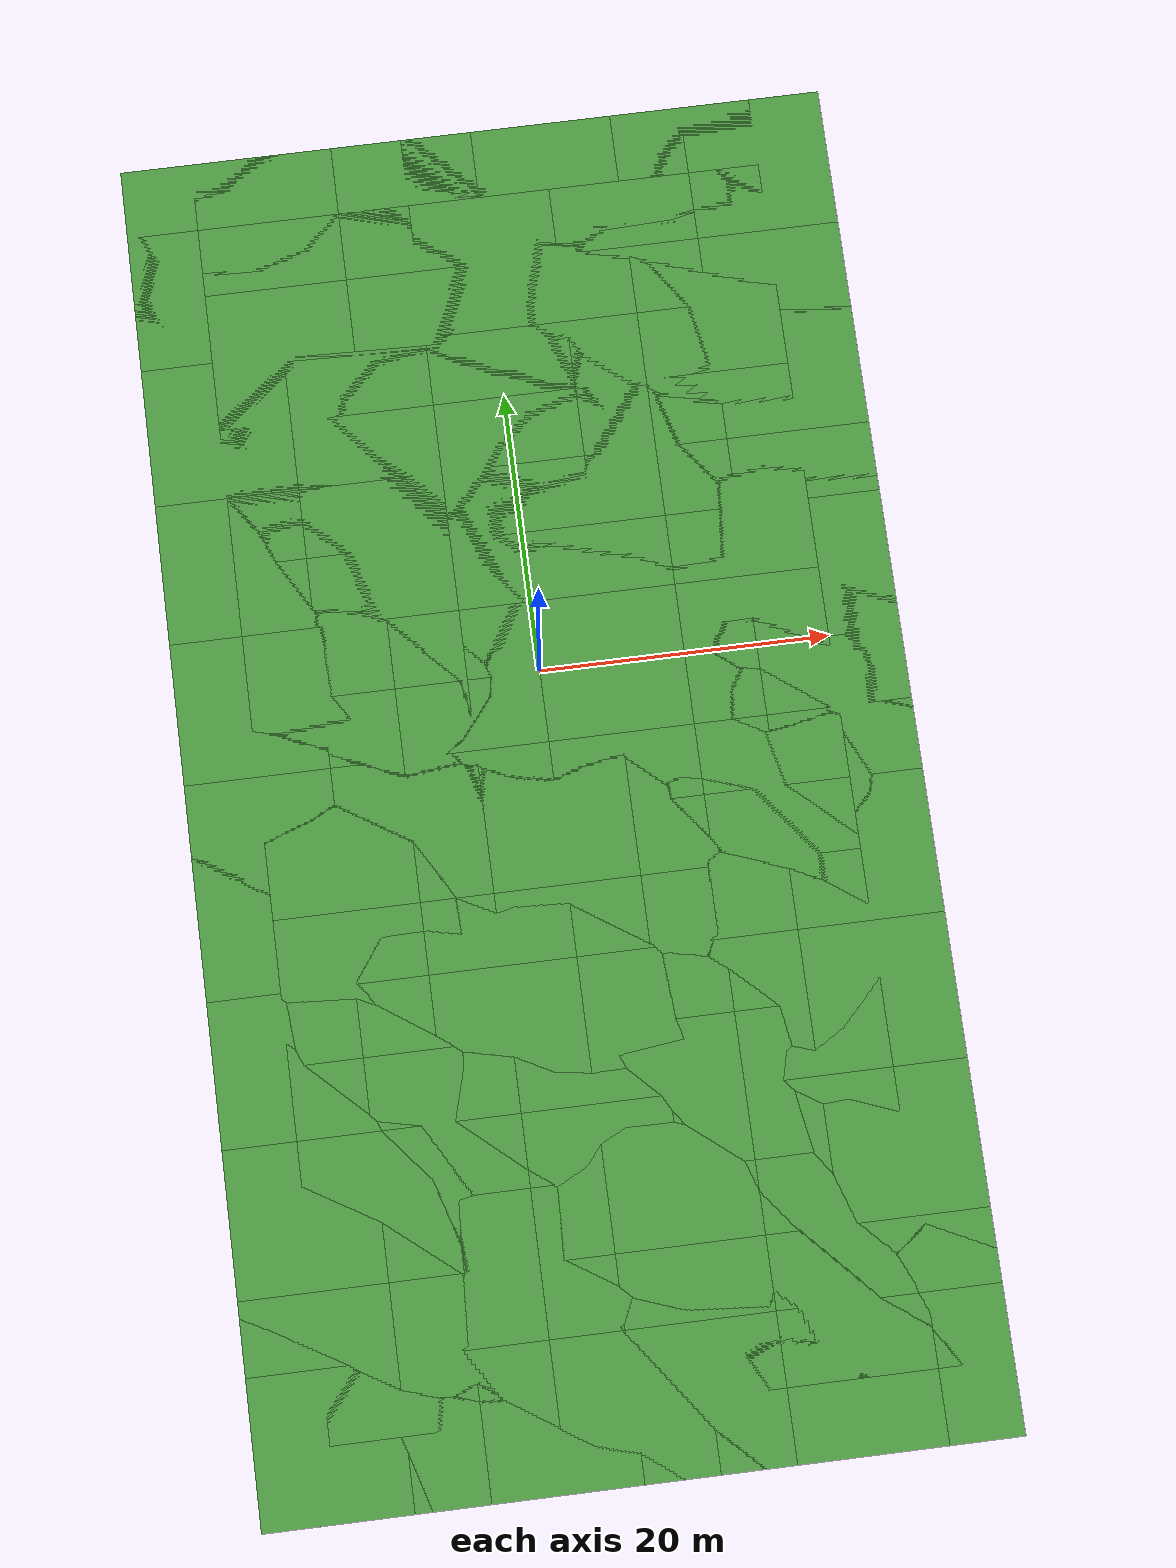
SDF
<sdf version="1.7">
 <world name="default">
  <physics name="ode_70iters" type="ode">
   <max_step_size>0.001</max_step_size>
   <real_time_update_rate>1000</real_time_update_rate>
   <ode>
    <solver>
     <type>quick</type>
     <iters>70</iters>
     <sor>1.3</sor>
     <use_dynamic_moi_rescaling>0</use_dynamic_moi_rescaling>
    </solver>
    <constraints>
     <cfm>0</cfm>
     <erp>0.2</erp>
     <contact_max_correcting_vel>100</contact_max_correcting_vel>
     <contact_surface_layer>0.001</contact_surface_layer>
    </constraints>
   </ode>
   <real_time_factor>1</real_time_factor>
  </physics>
  <model name="garden">
   <static>1</static>
   <pose>0 0 0 0 -0 1.57</pose>
   <frame name="garden_0::__model__" attached_to="garden_0::link">
    <pose relative_to="__model__">0 0 0 0 -0 0</pose>
   </frame>
   <static>1</static>
   <link name="garden_0::link">
    <collision name="collision">
     <geometry><plane><normal>0 0 1</normal><size>100 100</size></plane></geometry>
     <surface><friction><ode><mu>100</mu><mu2>50</mu2></ode></friction></surface>
    </collision>
    <visual name="visual_0">
     <cast_shadows>0</cast_shadows>
     <geometry><plane><normal>0 0 1</normal><size>10 10</size></plane></geometry>
     <material>
      <script>
       <uri>model://garden/materials/scripts</uri>
       <uri>model://garden/materials/textures</uri>
       <name>vrc/grass</name>
      </script>
     </material>
    </visual>
    <visual name="visual_1">
     <pose>5 0 0 0 -0 0</pose>
     <cast_shadows>0</cast_shadows>
     <geometry><plane><normal>0 0 1</normal><size>10 10</size></plane></geometry>
     <material>
      <script>
       <uri>model://garden/materials/scripts</uri>
       <uri>model://garden/materials/textures</uri>
       <name>vrc/grass</name>
      </script>
     </material>
    </visual>
    <visual name="visual_2">
     <pose>0 5 0 0 -0 0</pose>
     <cast_shadows>0</cast_shadows>
     <geometry><plane><normal>0 0 1</normal><size>10 10</size></plane></geometry>
     <material>
      <script>
       <uri>model://garden/materials/scripts</uri>
       <uri>model://garden/materials/textures</uri>
       <name>vrc/grass</name>
      </script>
     </material>
    </visual>
    <visual name="visual_3">
     <pose>-5 0 0 0 -0 0</pose>
     <cast_shadows>0</cast_shadows>
     <geometry><plane><normal>0 0 1</normal><size>10 10</size></plane></geometry>
     <material>
      <script>
       <uri>model://garden/materials/scripts</uri>
       <uri>model://garden/materials/textures</uri>
       <name>vrc/grass</name>
      </script>
     </material>
    </visual>
    <visual name="visual_4">
     <pose>0 -5 0 0 -0 0</pose>
     <cast_shadows>0</cast_shadows>
     <geometry><plane><normal>0 0 1</normal><size>10 10</size></plane></geometry>
     <material>
      <script>
       <uri>model://garden/materials/scripts</uri>
       <uri>model://garden/materials/textures</uri>
       <name>vrc/grass</name>
      </script>
     </material>
    </visual>
    <visual name="visual_5">
     <pose>5 5 0 0 -0 0</pose>
     <cast_shadows>0</cast_shadows>
     <geometry><plane><normal>0 0 1</normal><size>10 10</size></plane></geometry>
     <material>
      <script>
       <uri>model://garden/materials/scripts</uri>
       <uri>model://garden/materials/textures</uri>
       <name>vrc/grass</name>
      </script>
     </material>
    </visual>
    <visual name="visual_6">
     <pose>-5 -5 0 0 -0 0</pose>
     <cast_shadows>0</cast_shadows>
     <geometry><plane><normal>0 0 1</normal><size>10 10</size></plane></geometry>
     <material>
      <script>
       <uri>model://garden/materials/scripts</uri>
       <uri>model://garden/materials/textures</uri>
       <name>vrc/grass</name>
      </script>
     </material>
    </visual>
    <visual name="visual_7">
     <pose>5 -5 0 0 -0 0</pose>
     <cast_shadows>0</cast_shadows>
     <geometry><plane><normal>0 0 1</normal><size>10 10</size></plane></geometry>
     <material>
      <script>
       <uri>model://garden/materials/scripts</uri>
       <uri>model://garden/materials/textures</uri>
       <name>vrc/grass</name>
      </script>
     </material>
    </visual>
    <visual name="visual_8">
     <pose>-5 5 0 0 -0 0</pose>
     <cast_shadows>0</cast_shadows>
     <geometry><plane><normal>0 0 1</normal><size>10 10</size></plane></geometry>
     <material>
      <script>
       <uri>model://garden/materials/scripts</uri>
       <uri>model://garden/materials/textures</uri>
       <name>vrc/grass</name>
      </script>
     </material>
    </visual>
    <pose relative_to="garden_0::__model__">0 0 0 0 -0 0</pose>
   </link>
   <frame name="garden_1::__model__" attached_to="garden_1::link">
    <pose relative_to="__model__">15 0 0 0 -0 0</pose>
   </frame>
   <static>1</static>
   <link name="garden_1::link">
    <collision name="collision">
     <geometry><plane><normal>0 0 1</normal><size>100 100</size></plane></geometry>
     <surface><friction><ode><mu>100</mu><mu2>50</mu2></ode></friction></surface>
    </collision>
    <visual name="visual_0">
     <cast_shadows>0</cast_shadows>
     <geometry><plane><normal>0 0 1</normal><size>10 10</size></plane></geometry>
     <material>
      <script>
       <uri>model://garden/materials/scripts</uri>
       <uri>model://garden/materials/textures</uri>
       <name>vrc/grass</name>
      </script>
     </material>
    </visual>
    <visual name="visual_1">
     <pose>5 0 0 0 -0 0</pose>
     <cast_shadows>0</cast_shadows>
     <geometry><plane><normal>0 0 1</normal><size>10 10</size></plane></geometry>
     <material>
      <script>
       <uri>model://garden/materials/scripts</uri>
       <uri>model://garden/materials/textures</uri>
       <name>vrc/grass</name>
      </script>
     </material>
    </visual>
    <visual name="visual_2">
     <pose>0 5 0 0 -0 0</pose>
     <cast_shadows>0</cast_shadows>
     <geometry><plane><normal>0 0 1</normal><size>10 10</size></plane></geometry>
     <material>
      <script>
       <uri>model://garden/materials/scripts</uri>
       <uri>model://garden/materials/textures</uri>
       <name>vrc/grass</name>
      </script>
     </material>
    </visual>
    <visual name="visual_3">
     <pose>-5 0 0 0 -0 0</pose>
     <cast_shadows>0</cast_shadows>
     <geometry><plane><normal>0 0 1</normal><size>10 10</size></plane></geometry>
     <material>
      <script>
       <uri>model://garden/materials/scripts</uri>
       <uri>model://garden/materials/textures</uri>
       <name>vrc/grass</name>
      </script>
     </material>
    </visual>
    <visual name="visual_4">
     <pose>0 -5 0 0 -0 0</pose>
     <cast_shadows>0</cast_shadows>
     <geometry><plane><normal>0 0 1</normal><size>10 10</size></plane></geometry>
     <material>
      <script>
       <uri>model://garden/materials/scripts</uri>
       <uri>model://garden/materials/textures</uri>
       <name>vrc/grass</name>
      </script>
     </material>
    </visual>
    <visual name="visual_5">
     <pose>5 5 0 0 -0 0</pose>
     <cast_shadows>0</cast_shadows>
     <geometry><plane><normal>0 0 1</normal><size>10 10</size></plane></geometry>
     <material>
      <script>
       <uri>model://garden/materials/scripts</uri>
       <uri>model://garden/materials/textures</uri>
       <name>vrc/grass</name>
      </script>
     </material>
    </visual>
    <visual name="visual_6">
     <pose>-5 -5 0 0 -0 0</pose>
     <cast_shadows>0</cast_shadows>
     <geometry><plane><normal>0 0 1</normal><size>10 10</size></plane></geometry>
     <material>
      <script>
       <uri>model://garden/materials/scripts</uri>
       <uri>model://garden/materials/textures</uri>
       <name>vrc/grass</name>
      </script>
     </material>
    </visual>
    <visual name="visual_7">
     <pose>5 -5 0 0 -0 0</pose>
     <cast_shadows>0</cast_shadows>
     <geometry><plane><normal>0 0 1</normal><size>10 10</size></plane></geometry>
     <material>
      <script>
       <uri>model://garden/materials/scripts</uri>
       <uri>model://garden/materials/textures</uri>
       <name>vrc/grass</name>
      </script>
     </material>
    </visual>
    <visual name="visual_8">
     <pose>-5 5 0 0 -0 0</pose>
     <cast_shadows>0</cast_shadows>
     <geometry><plane><normal>0 0 1</normal><size>10 10</size></plane></geometry>
     <material>
      <script>
       <uri>model://garden/materials/scripts</uri>
       <uri>model://garden/materials/textures</uri>
       <name>vrc/grass</name>
      </script>
     </material>
    </visual>
    <pose relative_to="garden_1::__model__">0 0 0 0 -0 0</pose>
   </link>
   <frame name="garden_2::__model__" attached_to="garden_2::link">
    <pose relative_to="__model__">0 15 0 0 -0 0</pose>
   </frame>
   <static>1</static>
   <link name="garden_2::link">
    <collision name="collision">
     <geometry><plane><normal>0 0 1</normal><size>100 100</size></plane></geometry>
     <surface><friction><ode><mu>100</mu><mu2>50</mu2></ode></friction></surface>
    </collision>
    <visual name="visual_0">
     <cast_shadows>0</cast_shadows>
     <geometry><plane><normal>0 0 1</normal><size>10 10</size></plane></geometry>
     <material>
      <script>
       <uri>model://garden/materials/scripts</uri>
       <uri>model://garden/materials/textures</uri>
       <name>vrc/grass</name>
      </script>
     </material>
    </visual>
    <visual name="visual_1">
     <pose>5 0 0 0 -0 0</pose>
     <cast_shadows>0</cast_shadows>
     <geometry><plane><normal>0 0 1</normal><size>10 10</size></plane></geometry>
     <material>
      <script>
       <uri>model://garden/materials/scripts</uri>
       <uri>model://garden/materials/textures</uri>
       <name>vrc/grass</name>
      </script>
     </material>
    </visual>
    <visual name="visual_2">
     <pose>0 5 0 0 -0 0</pose>
     <cast_shadows>0</cast_shadows>
     <geometry><plane><normal>0 0 1</normal><size>10 10</size></plane></geometry>
     <material>
      <script>
       <uri>model://garden/materials/scripts</uri>
       <uri>model://garden/materials/textures</uri>
       <name>vrc/grass</name>
      </script>
     </material>
    </visual>
    <visual name="visual_3">
     <pose>-5 0 0 0 -0 0</pose>
     <cast_shadows>0</cast_shadows>
     <geometry><plane><normal>0 0 1</normal><size>10 10</size></plane></geometry>
     <material>
      <script>
       <uri>model://garden/materials/scripts</uri>
       <uri>model://garden/materials/textures</uri>
       <name>vrc/grass</name>
      </script>
     </material>
    </visual>
    <visual name="visual_4">
     <pose>0 -5 0 0 -0 0</pose>
     <cast_shadows>0</cast_shadows>
     <geometry><plane><normal>0 0 1</normal><size>10 10</size></plane></geometry>
     <material>
      <script>
       <uri>model://garden/materials/scripts</uri>
       <uri>model://garden/materials/textures</uri>
       <name>vrc/grass</name>
      </script>
     </material>
    </visual>
    <visual name="visual_5">
     <pose>5 5 0 0 -0 0</pose>
     <cast_shadows>0</cast_shadows>
     <geometry><plane><normal>0 0 1</normal><size>10 10</size></plane></geometry>
     <material>
      <script>
       <uri>model://garden/materials/scripts</uri>
       <uri>model://garden/materials/textures</uri>
       <name>vrc/grass</name>
      </script>
     </material>
    </visual>
    <visual name="visual_6">
     <pose>-5 -5 0 0 -0 0</pose>
     <cast_shadows>0</cast_shadows>
     <geometry><plane><normal>0 0 1</normal><size>10 10</size></plane></geometry>
     <material>
      <script>
       <uri>model://garden/materials/scripts</uri>
       <uri>model://garden/materials/textures</uri>
       <name>vrc/grass</name>
      </script>
     </material>
    </visual>
    <visual name="visual_7">
     <pose>5 -5 0 0 -0 0</pose>
     <cast_shadows>0</cast_shadows>
     <geometry><plane><normal>0 0 1</normal><size>10 10</size></plane></geometry>
     <material>
      <script>
       <uri>model://garden/materials/scripts</uri>
       <uri>model://garden/materials/textures</uri>
       <name>vrc/grass</name>
      </script>
     </material>
    </visual>
    <visual name="visual_8">
     <pose>-5 5 0 0 -0 0</pose>
     <cast_shadows>0</cast_shadows>
     <geometry><plane><normal>0 0 1</normal><size>10 10</size></plane></geometry>
     <material>
      <script>
       <uri>model://garden/materials/scripts</uri>
       <uri>model://garden/materials/textures</uri>
       <name>vrc/grass</name>
      </script>
     </material>
    </visual>
    <pose relative_to="garden_2::__model__">0 0 0 0 -0 0</pose>
   </link>
   <frame name="garden_3::__model__" attached_to="garden_3::link">
    <pose relative_to="__model__">0 -15 0 0 -0 0</pose>
   </frame>
   <static>1</static>
   <link name="garden_3::link">
    <collision name="collision">
     <geometry><plane><normal>0 0 1</normal><size>100 100</size></plane></geometry>
     <surface><friction><ode><mu>100</mu><mu2>50</mu2></ode></friction></surface>
    </collision>
    <visual name="visual_0">
     <cast_shadows>0</cast_shadows>
     <geometry><plane><normal>0 0 1</normal><size>10 10</size></plane></geometry>
     <material>
      <script>
       <uri>model://garden/materials/scripts</uri>
       <uri>model://garden/materials/textures</uri>
       <name>vrc/grass</name>
      </script>
     </material>
    </visual>
    <visual name="visual_1">
     <pose>5 0 0 0 -0 0</pose>
     <cast_shadows>0</cast_shadows>
     <geometry><plane><normal>0 0 1</normal><size>10 10</size></plane></geometry>
     <material>
      <script>
       <uri>model://garden/materials/scripts</uri>
       <uri>model://garden/materials/textures</uri>
       <name>vrc/grass</name>
      </script>
     </material>
    </visual>
    <visual name="visual_2">
     <pose>0 5 0 0 -0 0</pose>
     <cast_shadows>0</cast_shadows>
     <geometry><plane><normal>0 0 1</normal><size>10 10</size></plane></geometry>
     <material>
      <script>
       <uri>model://garden/materials/scripts</uri>
       <uri>model://garden/materials/textures</uri>
       <name>vrc/grass</name>
      </script>
     </material>
    </visual>
    <visual name="visual_3">
     <pose>-5 0 0 0 -0 0</pose>
     <cast_shadows>0</cast_shadows>
     <geometry><plane><normal>0 0 1</normal><size>10 10</size></plane></geometry>
     <material>
      <script>
       <uri>model://garden/materials/scripts</uri>
       <uri>model://garden/materials/textures</uri>
       <name>vrc/grass</name>
      </script>
     </material>
    </visual>
    <visual name="visual_4">
     <pose>0 -5 0 0 -0 0</pose>
     <cast_shadows>0</cast_shadows>
     <geometry><plane><normal>0 0 1</normal><size>10 10</size></plane></geometry>
     <material>
      <script>
       <uri>model://garden/materials/scripts</uri>
       <uri>model://garden/materials/textures</uri>
       <name>vrc/grass</name>
      </script>
     </material>
    </visual>
    <visual name="visual_5">
     <pose>5 5 0 0 -0 0</pose>
     <cast_shadows>0</cast_shadows>
     <geometry><plane><normal>0 0 1</normal><size>10 10</size></plane></geometry>
     <material>
      <script>
       <uri>model://garden/materials/scripts</uri>
       <uri>model://garden/materials/textures</uri>
       <name>vrc/grass</name>
      </script>
     </material>
    </visual>
    <visual name="visual_6">
     <pose>-5 -5 0 0 -0 0</pose>
     <cast_shadows>0</cast_shadows>
     <geometry><plane><normal>0 0 1</normal><size>10 10</size></plane></geometry>
     <material>
      <script>
       <uri>model://garden/materials/scripts</uri>
       <uri>model://garden/materials/textures</uri>
       <name>vrc/grass</name>
      </script>
     </material>
    </visual>
    <visual name="visual_7">
     <pose>5 -5 0 0 -0 0</pose>
     <cast_shadows>0</cast_shadows>
     <geometry><plane><normal>0 0 1</normal><size>10 10</size></plane></geometry>
     <material>
      <script>
       <uri>model://garden/materials/scripts</uri>
       <uri>model://garden/materials/textures</uri>
       <name>vrc/grass</name>
      </script>
     </material>
    </visual>
    <visual name="visual_8">
     <pose>-5 5 0 0 -0 0</pose>
     <cast_shadows>0</cast_shadows>
     <geometry><plane><normal>0 0 1</normal><size>10 10</size></plane></geometry>
     <material>
      <script>
       <uri>model://garden/materials/scripts</uri>
       <uri>model://garden/materials/textures</uri>
       <name>vrc/grass</name>
      </script>
     </material>
    </visual>
    <pose relative_to="garden_3::__model__">0 0 0 0 -0 0</pose>
   </link>
   <frame name="garden_4::__model__" attached_to="garden_4::link">
    <pose relative_to="__model__">-15 0 0 0 -0 0</pose>
   </frame>
   <static>1</static>
   <link name="garden_4::link">
    <collision name="collision">
     <geometry><plane><normal>0 0 1</normal><size>100 100</size></plane></geometry>
     <surface><friction><ode><mu>100</mu><mu2>50</mu2></ode></friction></surface>
    </collision>
    <visual name="visual_0">
     <cast_shadows>0</cast_shadows>
     <geometry><plane><normal>0 0 1</normal><size>10 10</size></plane></geometry>
     <material>
      <script>
       <uri>model://garden/materials/scripts</uri>
       <uri>model://garden/materials/textures</uri>
       <name>vrc/grass</name>
      </script>
     </material>
    </visual>
    <visual name="visual_1">
     <pose>5 0 0 0 -0 0</pose>
     <cast_shadows>0</cast_shadows>
     <geometry><plane><normal>0 0 1</normal><size>10 10</size></plane></geometry>
     <material>
      <script>
       <uri>model://garden/materials/scripts</uri>
       <uri>model://garden/materials/textures</uri>
       <name>vrc/grass</name>
      </script>
     </material>
    </visual>
    <visual name="visual_2">
     <pose>0 5 0 0 -0 0</pose>
     <cast_shadows>0</cast_shadows>
     <geometry><plane><normal>0 0 1</normal><size>10 10</size></plane></geometry>
     <material>
      <script>
       <uri>model://garden/materials/scripts</uri>
       <uri>model://garden/materials/textures</uri>
       <name>vrc/grass</name>
      </script>
     </material>
    </visual>
    <visual name="visual_3">
     <pose>-5 0 0 0 -0 0</pose>
     <cast_shadows>0</cast_shadows>
     <geometry><plane><normal>0 0 1</normal><size>10 10</size></plane></geometry>
     <material>
      <script>
       <uri>model://garden/materials/scripts</uri>
       <uri>model://garden/materials/textures</uri>
       <name>vrc/grass</name>
      </script>
     </material>
    </visual>
    <visual name="visual_4">
     <pose>0 -5 0 0 -0 0</pose>
     <cast_shadows>0</cast_shadows>
     <geometry><plane><normal>0 0 1</normal><size>10 10</size></plane></geometry>
     <material>
      <script>
       <uri>model://garden/materials/scripts</uri>
       <uri>model://garden/materials/textures</uri>
       <name>vrc/grass</name>
      </script>
     </material>
    </visual>
    <visual name="visual_5">
     <pose>5 5 0 0 -0 0</pose>
     <cast_shadows>0</cast_shadows>
     <geometry><plane><normal>0 0 1</normal><size>10 10</size></plane></geometry>
     <material>
      <script>
       <uri>model://garden/materials/scripts</uri>
       <uri>model://garden/materials/textures</uri>
       <name>vrc/grass</name>
      </script>
     </material>
    </visual>
    <visual name="visual_6">
     <pose>-5 -5 0 0 -0 0</pose>
     <cast_shadows>0</cast_shadows>
     <geometry><plane><normal>0 0 1</normal><size>10 10</size></plane></geometry>
     <material>
      <script>
       <uri>model://garden/materials/scripts</uri>
       <uri>model://garden/materials/textures</uri>
       <name>vrc/grass</name>
      </script>
     </material>
    </visual>
    <visual name="visual_7">
     <pose>5 -5 0 0 -0 0</pose>
     <cast_shadows>0</cast_shadows>
     <geometry><plane><normal>0 0 1</normal><size>10 10</size></plane></geometry>
     <material>
      <script>
       <uri>model://garden/materials/scripts</uri>
       <uri>model://garden/materials/textures</uri>
       <name>vrc/grass</name>
      </script>
     </material>
    </visual>
    <visual name="visual_8">
     <pose>-5 5 0 0 -0 0</pose>
     <cast_shadows>0</cast_shadows>
     <geometry><plane><normal>0 0 1</normal><size>10 10</size></plane></geometry>
     <material>
      <script>
       <uri>model://garden/materials/scripts</uri>
       <uri>model://garden/materials/textures</uri>
       <name>vrc/grass</name>
      </script>
     </material>
    </visual>
    <pose relative_to="garden_4::__model__">0 0 0 0 -0 0</pose>
   </link>
   <frame name="garden_5::__model__" attached_to="garden_5::link">
    <pose relative_to="__model__">15 15 0 0 -0 0</pose>
   </frame>
   <static>1</static>
   <link name="garden_5::link">
    <collision name="collision">
     <geometry><plane><normal>0 0 1</normal><size>100 100</size></plane></geometry>
     <surface><friction><ode><mu>100</mu><mu2>50</mu2></ode></friction></surface>
    </collision>
    <visual name="visual_0">
     <cast_shadows>0</cast_shadows>
     <geometry><plane><normal>0 0 1</normal><size>10 10</size></plane></geometry>
     <material>
      <script>
       <uri>model://garden/materials/scripts</uri>
       <uri>model://garden/materials/textures</uri>
       <name>vrc/grass</name>
      </script>
     </material>
    </visual>
    <visual name="visual_1">
     <pose>5 0 0 0 -0 0</pose>
     <cast_shadows>0</cast_shadows>
     <geometry><plane><normal>0 0 1</normal><size>10 10</size></plane></geometry>
     <material>
      <script>
       <uri>model://garden/materials/scripts</uri>
       <uri>model://garden/materials/textures</uri>
       <name>vrc/grass</name>
      </script>
     </material>
    </visual>
    <visual name="visual_2">
     <pose>0 5 0 0 -0 0</pose>
     <cast_shadows>0</cast_shadows>
     <geometry><plane><normal>0 0 1</normal><size>10 10</size></plane></geometry>
     <material>
      <script>
       <uri>model://garden/materials/scripts</uri>
       <uri>model://garden/materials/textures</uri>
       <name>vrc/grass</name>
      </script>
     </material>
    </visual>
    <visual name="visual_3">
     <pose>-5 0 0 0 -0 0</pose>
     <cast_shadows>0</cast_shadows>
     <geometry><plane><normal>0 0 1</normal><size>10 10</size></plane></geometry>
     <material>
      <script>
       <uri>model://garden/materials/scripts</uri>
       <uri>model://garden/materials/textures</uri>
       <name>vrc/grass</name>
      </script>
     </material>
    </visual>
    <visual name="visual_4">
     <pose>0 -5 0 0 -0 0</pose>
     <cast_shadows>0</cast_shadows>
     <geometry><plane><normal>0 0 1</normal><size>10 10</size></plane></geometry>
     <material>
      <script>
       <uri>model://garden/materials/scripts</uri>
       <uri>model://garden/materials/textures</uri>
       <name>vrc/grass</name>
      </script>
     </material>
    </visual>
    <visual name="visual_5">
     <pose>5 5 0 0 -0 0</pose>
     <cast_shadows>0</cast_shadows>
     <geometry><plane><normal>0 0 1</normal><size>10 10</size></plane></geometry>
     <material>
      <script>
       <uri>model://garden/materials/scripts</uri>
       <uri>model://garden/materials/textures</uri>
       <name>vrc/grass</name>
      </script>
     </material>
    </visual>
    <visual name="visual_6">
     <pose>-5 -5 0 0 -0 0</pose>
     <cast_shadows>0</cast_shadows>
     <geometry><plane><normal>0 0 1</normal><size>10 10</size></plane></geometry>
     <material>
      <script>
       <uri>model://garden/materials/scripts</uri>
       <uri>model://garden/materials/textures</uri>
       <name>vrc/grass</name>
      </script>
     </material>
    </visual>
    <visual name="visual_7">
     <pose>5 -5 0 0 -0 0</pose>
     <cast_shadows>0</cast_shadows>
     <geometry><plane><normal>0 0 1</normal><size>10 10</size></plane></geometry>
     <material>
      <script>
       <uri>model://garden/materials/scripts</uri>
       <uri>model://garden/materials/textures</uri>
       <name>vrc/grass</name>
      </script>
     </material>
    </visual>
    <visual name="visual_8">
     <pose>-5 5 0 0 -0 0</pose>
     <cast_shadows>0</cast_shadows>
     <geometry><plane><normal>0 0 1</normal><size>10 10</size></plane></geometry>
     <material>
      <script>
       <uri>model://garden/materials/scripts</uri>
       <uri>model://garden/materials/textures</uri>
       <name>vrc/grass</name>
      </script>
     </material>
    </visual>
    <pose relative_to="garden_5::__model__">0 0 0 0 -0 0</pose>
   </link>
   <frame name="garden_6::__model__" attached_to="garden_6::link">
    <pose relative_to="__model__">-15 -15 0 0 -0 0</pose>
   </frame>
   <static>1</static>
   <link name="garden_6::link">
    <collision name="collision">
     <geometry><plane><normal>0 0 1</normal><size>100 100</size></plane></geometry>
     <surface><friction><ode><mu>100</mu><mu2>50</mu2></ode></friction></surface>
    </collision>
    <visual name="visual_0">
     <cast_shadows>0</cast_shadows>
     <geometry><plane><normal>0 0 1</normal><size>10 10</size></plane></geometry>
     <material>
      <script>
       <uri>model://garden/materials/scripts</uri>
       <uri>model://garden/materials/textures</uri>
       <name>vrc/grass</name>
      </script>
     </material>
    </visual>
    <visual name="visual_1">
     <pose>5 0 0 0 -0 0</pose>
     <cast_shadows>0</cast_shadows>
     <geometry><plane><normal>0 0 1</normal><size>10 10</size></plane></geometry>
     <material>
      <script>
       <uri>model://garden/materials/scripts</uri>
       <uri>model://garden/materials/textures</uri>
       <name>vrc/grass</name>
      </script>
     </material>
    </visual>
    <visual name="visual_2">
     <pose>0 5 0 0 -0 0</pose>
     <cast_shadows>0</cast_shadows>
     <geometry><plane><normal>0 0 1</normal><size>10 10</size></plane></geometry>
     <material>
      <script>
       <uri>model://garden/materials/scripts</uri>
       <uri>model://garden/materials/textures</uri>
       <name>vrc/grass</name>
      </script>
     </material>
    </visual>
    <visual name="visual_3">
     <pose>-5 0 0 0 -0 0</pose>
     <cast_shadows>0</cast_shadows>
     <geometry><plane><normal>0 0 1</normal><size>10 10</size></plane></geometry>
     <material>
      <script>
       <uri>model://garden/materials/scripts</uri>
       <uri>model://garden/materials/textures</uri>
       <name>vrc/grass</name>
      </script>
     </material>
    </visual>
    <visual name="visual_4">
     <pose>0 -5 0 0 -0 0</pose>
     <cast_shadows>0</cast_shadows>
     <geometry><plane><normal>0 0 1</normal><size>10 10</size></plane></geometry>
     <material>
      <script>
       <uri>model://garden/materials/scripts</uri>
       <uri>model://garden/materials/textures</uri>
       <name>vrc/grass</name>
      </script>
     </material>
    </visual>
    <visual name="visual_5">
     <pose>5 5 0 0 -0 0</pose>
     <cast_shadows>0</cast_shadows>
     <geometry><plane><normal>0 0 1</normal><size>10 10</size></plane></geometry>
     <material>
      <script>
       <uri>model://garden/materials/scripts</uri>
       <uri>model://garden/materials/textures</uri>
       <name>vrc/grass</name>
      </script>
     </material>
    </visual>
    <visual name="visual_6">
     <pose>-5 -5 0 0 -0 0</pose>
     <cast_shadows>0</cast_shadows>
     <geometry><plane><normal>0 0 1</normal><size>10 10</size></plane></geometry>
     <material>
      <script>
       <uri>model://garden/materials/scripts</uri>
       <uri>model://garden/materials/textures</uri>
       <name>vrc/grass</name>
      </script>
     </material>
    </visual>
    <visual name="visual_7">
     <pose>5 -5 0 0 -0 0</pose>
     <cast_shadows>0</cast_shadows>
     <geometry><plane><normal>0 0 1</normal><size>10 10</size></plane></geometry>
     <material>
      <script>
       <uri>model://garden/materials/scripts</uri>
       <uri>model://garden/materials/textures</uri>
       <name>vrc/grass</name>
      </script>
     </material>
    </visual>
    <visual name="visual_8">
     <pose>-5 5 0 0 -0 0</pose>
     <cast_shadows>0</cast_shadows>
     <geometry><plane><normal>0 0 1</normal><size>10 10</size></plane></geometry>
     <material>
      <script>
       <uri>model://garden/materials/scripts</uri>
       <uri>model://garden/materials/textures</uri>
       <name>vrc/grass</name>
      </script>
     </material>
    </visual>
    <pose relative_to="garden_6::__model__">0 0 0 0 -0 0</pose>
   </link>
   <frame name="garden_7::__model__" attached_to="garden_7::link">
    <pose relative_to="__model__">-15 15 0 0 -0 0</pose>
   </frame>
   <static>1</static>
   <link name="garden_7::link">
    <collision name="collision">
     <geometry><plane><normal>0 0 1</normal><size>100 100</size></plane></geometry>
     <surface><friction><ode><mu>100</mu><mu2>50</mu2></ode></friction></surface>
    </collision>
    <visual name="visual_0">
     <cast_shadows>0</cast_shadows>
     <geometry><plane><normal>0 0 1</normal><size>10 10</size></plane></geometry>
     <material>
      <script>
       <uri>model://garden/materials/scripts</uri>
       <uri>model://garden/materials/textures</uri>
       <name>vrc/grass</name>
      </script>
     </material>
    </visual>
    <visual name="visual_1">
     <pose>5 0 0 0 -0 0</pose>
     <cast_shadows>0</cast_shadows>
     <geometry><plane><normal>0 0 1</normal><size>10 10</size></plane></geometry>
     <material>
      <script>
       <uri>model://garden/materials/scripts</uri>
       <uri>model://garden/materials/textures</uri>
       <name>vrc/grass</name>
      </script>
     </material>
    </visual>
    <visual name="visual_2">
     <pose>0 5 0 0 -0 0</pose>
     <cast_shadows>0</cast_shadows>
     <geometry><plane><normal>0 0 1</normal><size>10 10</size></plane></geometry>
     <material>
      <script>
       <uri>model://garden/materials/scripts</uri>
       <uri>model://garden/materials/textures</uri>
       <name>vrc/grass</name>
      </script>
     </material>
    </visual>
    <visual name="visual_3">
     <pose>-5 0 0 0 -0 0</pose>
     <cast_shadows>0</cast_shadows>
     <geometry><plane><normal>0 0 1</normal><size>10 10</size></plane></geometry>
     <material>
      <script>
       <uri>model://garden/materials/scripts</uri>
       <uri>model://garden/materials/textures</uri>
       <name>vrc/grass</name>
      </script>
     </material>
    </visual>
    <visual name="visual_4">
     <pose>0 -5 0 0 -0 0</pose>
     <cast_shadows>0</cast_shadows>
     <geometry><plane><normal>0 0 1</normal><size>10 10</size></plane></geometry>
     <material>
      <script>
       <uri>model://garden/materials/scripts</uri>
       <uri>model://garden/materials/textures</uri>
       <name>vrc/grass</name>
      </script>
     </material>
    </visual>
    <visual name="visual_5">
     <pose>5 5 0 0 -0 0</pose>
     <cast_shadows>0</cast_shadows>
     <geometry><plane><normal>0 0 1</normal><size>10 10</size></plane></geometry>
     <material>
      <script>
       <uri>model://garden/materials/scripts</uri>
       <uri>model://garden/materials/textures</uri>
       <name>vrc/grass</name>
      </script>
     </material>
    </visual>
    <visual name="visual_6">
     <pose>-5 -5 0 0 -0 0</pose>
     <cast_shadows>0</cast_shadows>
     <geometry><plane><normal>0 0 1</normal><size>10 10</size></plane></geometry>
     <material>
      <script>
       <uri>model://garden/materials/scripts</uri>
       <uri>model://garden/materials/textures</uri>
       <name>vrc/grass</name>
      </script>
     </material>
    </visual>
    <visual name="visual_7">
     <pose>5 -5 0 0 -0 0</pose>
     <cast_shadows>0</cast_shadows>
     <geometry><plane><normal>0 0 1</normal><size>10 10</size></plane></geometry>
     <material>
      <script>
       <uri>model://garden/materials/scripts</uri>
       <uri>model://garden/materials/textures</uri>
       <name>vrc/grass</name>
      </script>
     </material>
    </visual>
    <visual name="visual_8">
     <pose>-5 5 0 0 -0 0</pose>
     <cast_shadows>0</cast_shadows>
     <geometry><plane><normal>0 0 1</normal><size>10 10</size></plane></geometry>
     <material>
      <script>
       <uri>model://garden/materials/scripts</uri>
       <uri>model://garden/materials/textures</uri>
       <name>vrc/grass</name>
      </script>
     </material>
    </visual>
    <pose relative_to="garden_7::__model__">0 0 0 0 -0 0</pose>
   </link>
   <frame name="garden_8::__model__" attached_to="garden_8::link">
    <pose relative_to="__model__">15 -15 0 0 -0 0</pose>
   </frame>
   <static>1</static>
   <link name="garden_8::link">
    <collision name="collision">
     <geometry><plane><normal>0 0 1</normal><size>100 100</size></plane></geometry>
     <surface><friction><ode><mu>100</mu><mu2>50</mu2></ode></friction></surface>
    </collision>
    <visual name="visual_0">
     <cast_shadows>0</cast_shadows>
     <geometry><plane><normal>0 0 1</normal><size>10 10</size></plane></geometry>
     <material>
      <script>
       <uri>model://garden/materials/scripts</uri>
       <uri>model://garden/materials/textures</uri>
       <name>vrc/grass</name>
      </script>
     </material>
    </visual>
    <visual name="visual_1">
     <pose>5 0 0 0 -0 0</pose>
     <cast_shadows>0</cast_shadows>
     <geometry><plane><normal>0 0 1</normal><size>10 10</size></plane></geometry>
     <material>
      <script>
       <uri>model://garden/materials/scripts</uri>
       <uri>model://garden/materials/textures</uri>
       <name>vrc/grass</name>
      </script>
     </material>
    </visual>
    <visual name="visual_2">
     <pose>0 5 0 0 -0 0</pose>
     <cast_shadows>0</cast_shadows>
     <geometry><plane><normal>0 0 1</normal><size>10 10</size></plane></geometry>
     <material>
      <script>
       <uri>model://garden/materials/scripts</uri>
       <uri>model://garden/materials/textures</uri>
       <name>vrc/grass</name>
      </script>
     </material>
    </visual>
    <visual name="visual_3">
     <pose>-5 0 0 0 -0 0</pose>
     <cast_shadows>0</cast_shadows>
     <geometry><plane><normal>0 0 1</normal><size>10 10</size></plane></geometry>
     <material>
      <script>
       <uri>model://garden/materials/scripts</uri>
       <uri>model://garden/materials/textures</uri>
       <name>vrc/grass</name>
      </script>
     </material>
    </visual>
    <visual name="visual_4">
     <pose>0 -5 0 0 -0 0</pose>
     <cast_shadows>0</cast_shadows>
     <geometry><plane><normal>0 0 1</normal><size>10 10</size></plane></geometry>
     <material>
      <script>
       <uri>model://garden/materials/scripts</uri>
       <uri>model://garden/materials/textures</uri>
       <name>vrc/grass</name>
      </script>
     </material>
    </visual>
    <visual name="visual_5">
     <pose>5 5 0 0 -0 0</pose>
     <cast_shadows>0</cast_shadows>
     <geometry><plane><normal>0 0 1</normal><size>10 10</size></plane></geometry>
     <material>
      <script>
       <uri>model://garden/materials/scripts</uri>
       <uri>model://garden/materials/textures</uri>
       <name>vrc/grass</name>
      </script>
     </material>
    </visual>
    <visual name="visual_6">
     <pose>-5 -5 0 0 -0 0</pose>
     <cast_shadows>0</cast_shadows>
     <geometry><plane><normal>0 0 1</normal><size>10 10</size></plane></geometry>
     <material>
      <script>
       <uri>model://garden/materials/scripts</uri>
       <uri>model://garden/materials/textures</uri>
       <name>vrc/grass</name>
      </script>
     </material>
    </visual>
    <visual name="visual_7">
     <pose>5 -5 0 0 -0 0</pose>
     <cast_shadows>0</cast_shadows>
     <geometry><plane><normal>0 0 1</normal><size>10 10</size></plane></geometry>
     <material>
      <script>
       <uri>model://garden/materials/scripts</uri>
       <uri>model://garden/materials/textures</uri>
       <name>vrc/grass</name>
      </script>
     </material>
    </visual>
    <visual name="visual_8">
     <pose>-5 5 0 0 -0 0</pose>
     <cast_shadows>0</cast_shadows>
     <geometry><plane><normal>0 0 1</normal><size>10 10</size></plane></geometry>
     <material>
      <script>
       <uri>model://garden/materials/scripts</uri>
       <uri>model://garden/materials/textures</uri>
       <name>vrc/grass</name>
      </script>
     </material>
    </visual>
    <pose relative_to="garden_8::__model__">0 0 0 0 -0 0</pose>
   </link>
   <frame name="garden_9::__model__" attached_to="garden_9::link">
    <pose relative_to="__model__">-30 -15 0 0 -0 0</pose>
   </frame>
   <static>1</static>
   <link name="garden_9::link">
    <collision name="collision">
     <geometry><plane><normal>0 0 1</normal><size>100 100</size></plane></geometry>
     <surface><friction><ode><mu>100</mu><mu2>50</mu2></ode></friction></surface>
    </collision>
    <visual name="visual_0">
     <cast_shadows>0</cast_shadows>
     <geometry><plane><normal>0 0 1</normal><size>10 10</size></plane></geometry>
     <material>
      <script>
       <uri>model://garden/materials/scripts</uri>
       <uri>model://garden/materials/textures</uri>
       <name>vrc/grass</name>
      </script>
     </material>
    </visual>
    <visual name="visual_1">
     <pose>5 0 0 0 -0 0</pose>
     <cast_shadows>0</cast_shadows>
     <geometry><plane><normal>0 0 1</normal><size>10 10</size></plane></geometry>
     <material>
      <script>
       <uri>model://garden/materials/scripts</uri>
       <uri>model://garden/materials/textures</uri>
       <name>vrc/grass</name>
      </script>
     </material>
    </visual>
    <visual name="visual_2">
     <pose>0 5 0 0 -0 0</pose>
     <cast_shadows>0</cast_shadows>
     <geometry><plane><normal>0 0 1</normal><size>10 10</size></plane></geometry>
     <material>
      <script>
       <uri>model://garden/materials/scripts</uri>
       <uri>model://garden/materials/textures</uri>
       <name>vrc/grass</name>
      </script>
     </material>
    </visual>
    <visual name="visual_3">
     <pose>-5 0 0 0 -0 0</pose>
     <cast_shadows>0</cast_shadows>
     <geometry><plane><normal>0 0 1</normal><size>10 10</size></plane></geometry>
     <material>
      <script>
       <uri>model://garden/materials/scripts</uri>
       <uri>model://garden/materials/textures</uri>
       <name>vrc/grass</name>
      </script>
     </material>
    </visual>
    <visual name="visual_4">
     <pose>0 -5 0 0 -0 0</pose>
     <cast_shadows>0</cast_shadows>
     <geometry><plane><normal>0 0 1</normal><size>10 10</size></plane></geometry>
     <material>
      <script>
       <uri>model://garden/materials/scripts</uri>
       <uri>model://garden/materials/textures</uri>
       <name>vrc/grass</name>
      </script>
     </material>
    </visual>
    <visual name="visual_5">
     <pose>5 5 0 0 -0 0</pose>
     <cast_shadows>0</cast_shadows>
     <geometry><plane><normal>0 0 1</normal><size>10 10</size></plane></geometry>
     <material>
      <script>
       <uri>model://garden/materials/scripts</uri>
       <uri>model://garden/materials/textures</uri>
       <name>vrc/grass</name>
      </script>
     </material>
    </visual>
    <visual name="visual_6">
     <pose>-5 -5 0 0 -0 0</pose>
     <cast_shadows>0</cast_shadows>
     <geometry><plane><normal>0 0 1</normal><size>10 10</size></plane></geometry>
     <material>
      <script>
       <uri>model://garden/materials/scripts</uri>
       <uri>model://garden/materials/textures</uri>
       <name>vrc/grass</name>
      </script>
     </material>
    </visual>
    <visual name="visual_7">
     <pose>5 -5 0 0 -0 0</pose>
     <cast_shadows>0</cast_shadows>
     <geometry><plane><normal>0 0 1</normal><size>10 10</size></plane></geometry>
     <material>
      <script>
       <uri>model://garden/materials/scripts</uri>
       <uri>model://garden/materials/textures</uri>
       <name>vrc/grass</name>
      </script>
     </material>
    </visual>
    <visual name="visual_8">
     <pose>-5 5 0 0 -0 0</pose>
     <cast_shadows>0</cast_shadows>
     <geometry><plane><normal>0 0 1</normal><size>10 10</size></plane></geometry>
     <material>
      <script>
       <uri>model://garden/materials/scripts</uri>
       <uri>model://garden/materials/textures</uri>
       <name>vrc/grass</name>
      </script>
     </material>
    </visual>
    <pose relative_to="garden_9::__model__">0 0 0 0 -0 0</pose>
   </link>
   <frame name="garden_10::__model__" attached_to="garden_10::link">
    <pose relative_to="__model__">-30 0 0 0 -0 0</pose>
   </frame>
   <static>1</static>
   <link name="garden_10::link">
    <collision name="collision">
     <geometry><plane><normal>0 0 1</normal><size>100 100</size></plane></geometry>
     <surface><friction><ode><mu>100</mu><mu2>50</mu2></ode></friction></surface>
    </collision>
    <visual name="visual_0">
     <cast_shadows>0</cast_shadows>
     <geometry><plane><normal>0 0 1</normal><size>10 10</size></plane></geometry>
     <material>
      <script>
       <uri>model://garden/materials/scripts</uri>
       <uri>model://garden/materials/textures</uri>
       <name>vrc/grass</name>
      </script>
     </material>
    </visual>
    <visual name="visual_1">
     <pose>5 0 0 0 -0 0</pose>
     <cast_shadows>0</cast_shadows>
     <geometry><plane><normal>0 0 1</normal><size>10 10</size></plane></geometry>
     <material>
      <script>
       <uri>model://garden/materials/scripts</uri>
       <uri>model://garden/materials/textures</uri>
       <name>vrc/grass</name>
      </script>
     </material>
    </visual>
    <visual name="visual_2">
     <pose>0 5 0 0 -0 0</pose>
     <cast_shadows>0</cast_shadows>
     <geometry><plane><normal>0 0 1</normal><size>10 10</size></plane></geometry>
     <material>
      <script>
       <uri>model://garden/materials/scripts</uri>
       <uri>model://garden/materials/textures</uri>
       <name>vrc/grass</name>
      </script>
     </material>
    </visual>
    <visual name="visual_3">
     <pose>-5 0 0 0 -0 0</pose>
     <cast_shadows>0</cast_shadows>
     <geometry><plane><normal>0 0 1</normal><size>10 10</size></plane></geometry>
     <material>
      <script>
       <uri>model://garden/materials/scripts</uri>
       <uri>model://garden/materials/textures</uri>
       <name>vrc/grass</name>
      </script>
     </material>
    </visual>
    <visual name="visual_4">
     <pose>0 -5 0 0 -0 0</pose>
     <cast_shadows>0</cast_shadows>
     <geometry><plane><normal>0 0 1</normal><size>10 10</size></plane></geometry>
     <material>
      <script>
       <uri>model://garden/materials/scripts</uri>
       <uri>model://garden/materials/textures</uri>
       <name>vrc/grass</name>
      </script>
     </material>
    </visual>
    <visual name="visual_5">
     <pose>5 5 0 0 -0 0</pose>
     <cast_shadows>0</cast_shadows>
     <geometry><plane><normal>0 0 1</normal><size>10 10</size></plane></geometry>
     <material>
      <script>
       <uri>model://garden/materials/scripts</uri>
       <uri>model://garden/materials/textures</uri>
       <name>vrc/grass</name>
      </script>
     </material>
    </visual>
    <visual name="visual_6">
     <pose>-5 -5 0 0 -0 0</pose>
     <cast_shadows>0</cast_shadows>
     <geometry><plane><normal>0 0 1</normal><size>10 10</size></plane></geometry>
     <material>
      <script>
       <uri>model://garden/materials/scripts</uri>
       <uri>model://garden/materials/textures</uri>
       <name>vrc/grass</name>
      </script>
     </material>
    </visual>
    <visual name="visual_7">
     <pose>5 -5 0 0 -0 0</pose>
     <cast_shadows>0</cast_shadows>
     <geometry><plane><normal>0 0 1</normal><size>10 10</size></plane></geometry>
     <material>
      <script>
       <uri>model://garden/materials/scripts</uri>
       <uri>model://garden/materials/textures</uri>
       <name>vrc/grass</name>
      </script>
     </material>
    </visual>
    <visual name="visual_8">
     <pose>-5 5 0 0 -0 0</pose>
     <cast_shadows>0</cast_shadows>
     <geometry><plane><normal>0 0 1</normal><size>10 10</size></plane></geometry>
     <material>
      <script>
       <uri>model://garden/materials/scripts</uri>
       <uri>model://garden/materials/textures</uri>
       <name>vrc/grass</name>
      </script>
     </material>
    </visual>
    <pose relative_to="garden_10::__model__">0 0 0 0 -0 0</pose>
   </link>
   <frame name="garden_11::__model__" attached_to="garden_11::link">
    <pose relative_to="__model__">-30 15 0 0 -0 0</pose>
   </frame>
   <static>1</static>
   <link name="garden_11::link">
    <collision name="collision">
     <geometry><plane><normal>0 0 1</normal><size>100 100</size></plane></geometry>
     <surface><friction><ode><mu>100</mu><mu2>50</mu2></ode></friction></surface>
    </collision>
    <visual name="visual_0">
     <cast_shadows>0</cast_shadows>
     <geometry><plane><normal>0 0 1</normal><size>10 10</size></plane></geometry>
     <material>
      <script>
       <uri>model://garden/materials/scripts</uri>
       <uri>model://garden/materials/textures</uri>
       <name>vrc/grass</name>
      </script>
     </material>
    </visual>
    <visual name="visual_1">
     <pose>5 0 0 0 -0 0</pose>
     <cast_shadows>0</cast_shadows>
     <geometry><plane><normal>0 0 1</normal><size>10 10</size></plane></geometry>
     <material>
      <script>
       <uri>model://garden/materials/scripts</uri>
       <uri>model://garden/materials/textures</uri>
       <name>vrc/grass</name>
      </script>
     </material>
    </visual>
    <visual name="visual_2">
     <pose>0 5 0 0 -0 0</pose>
     <cast_shadows>0</cast_shadows>
     <geometry><plane><normal>0 0 1</normal><size>10 10</size></plane></geometry>
     <material>
      <script>
       <uri>model://garden/materials/scripts</uri>
       <uri>model://garden/materials/textures</uri>
       <name>vrc/grass</name>
      </script>
     </material>
    </visual>
    <visual name="visual_3">
     <pose>-5 0 0 0 -0 0</pose>
     <cast_shadows>0</cast_shadows>
     <geometry><plane><normal>0 0 1</normal><size>10 10</size></plane></geometry>
     <material>
      <script>
       <uri>model://garden/materials/scripts</uri>
       <uri>model://garden/materials/textures</uri>
       <name>vrc/grass</name>
      </script>
     </material>
    </visual>
    <visual name="visual_4">
     <pose>0 -5 0 0 -0 0</pose>
     <cast_shadows>0</cast_shadows>
     <geometry><plane><normal>0 0 1</normal><size>10 10</size></plane></geometry>
     <material>
      <script>
       <uri>model://garden/materials/scripts</uri>
       <uri>model://garden/materials/textures</uri>
       <name>vrc/grass</name>
      </script>
     </material>
    </visual>
    <visual name="visual_5">
     <pose>5 5 0 0 -0 0</pose>
     <cast_shadows>0</cast_shadows>
     <geometry><plane><normal>0 0 1</normal><size>10 10</size></plane></geometry>
     <material>
      <script>
       <uri>model://garden/materials/scripts</uri>
       <uri>model://garden/materials/textures</uri>
       <name>vrc/grass</name>
      </script>
     </material>
    </visual>
    <visual name="visual_6">
     <pose>-5 -5 0 0 -0 0</pose>
     <cast_shadows>0</cast_shadows>
     <geometry><plane><normal>0 0 1</normal><size>10 10</size></plane></geometry>
     <material>
      <script>
       <uri>model://garden/materials/scripts</uri>
       <uri>model://garden/materials/textures</uri>
       <name>vrc/grass</name>
      </script>
     </material>
    </visual>
    <visual name="visual_7">
     <pose>5 -5 0 0 -0 0</pose>
     <cast_shadows>0</cast_shadows>
     <geometry><plane><normal>0 0 1</normal><size>10 10</size></plane></geometry>
     <material>
      <script>
       <uri>model://garden/materials/scripts</uri>
       <uri>model://garden/materials/textures</uri>
       <name>vrc/grass</name>
      </script>
     </material>
    </visual>
    <visual name="visual_8">
     <pose>-5 5 0 0 -0 0</pose>
     <cast_shadows>0</cast_shadows>
     <geometry><plane><normal>0 0 1</normal><size>10 10</size></plane></geometry>
     <material>
      <script>
       <uri>model://garden/materials/scripts</uri>
       <uri>model://garden/materials/textures</uri>
       <name>vrc/grass</name>
      </script>
     </material>
    </visual>
    <pose relative_to="garden_11::__model__">0 0 0 0 -0 0</pose>
   </link>
   <frame name="garden_12::__model__" attached_to="garden_12::link">
    <pose relative_to="__model__">-45 -15 0 0 -0 0</pose>
   </frame>
   <static>1</static>
   <link name="garden_12::link">
    <collision name="collision">
     <geometry><plane><normal>0 0 1</normal><size>100 100</size></plane></geometry>
     <surface><friction><ode><mu>100</mu><mu2>50</mu2></ode></friction></surface>
    </collision>
    <visual name="visual_0">
     <cast_shadows>0</cast_shadows>
     <geometry><plane><normal>0 0 1</normal><size>10 10</size></plane></geometry>
     <material>
      <script>
       <uri>model://garden/materials/scripts</uri>
       <uri>model://garden/materials/textures</uri>
       <name>vrc/grass</name>
      </script>
     </material>
    </visual>
    <visual name="visual_1">
     <pose>5 0 0 0 -0 0</pose>
     <cast_shadows>0</cast_shadows>
     <geometry><plane><normal>0 0 1</normal><size>10 10</size></plane></geometry>
     <material>
      <script>
       <uri>model://garden/materials/scripts</uri>
       <uri>model://garden/materials/textures</uri>
       <name>vrc/grass</name>
      </script>
     </material>
    </visual>
    <visual name="visual_2">
     <pose>0 5 0 0 -0 0</pose>
     <cast_shadows>0</cast_shadows>
     <geometry><plane><normal>0 0 1</normal><size>10 10</size></plane></geometry>
     <material>
      <script>
       <uri>model://garden/materials/scripts</uri>
       <uri>model://garden/materials/textures</uri>
       <name>vrc/grass</name>
      </script>
     </material>
    </visual>
    <visual name="visual_3">
     <pose>-5 0 0 0 -0 0</pose>
     <cast_shadows>0</cast_shadows>
     <geometry><plane><normal>0 0 1</normal><size>10 10</size></plane></geometry>
     <material>
      <script>
       <uri>model://garden/materials/scripts</uri>
       <uri>model://garden/materials/textures</uri>
       <name>vrc/grass</name>
      </script>
     </material>
    </visual>
    <visual name="visual_4">
     <pose>0 -5 0 0 -0 0</pose>
     <cast_shadows>0</cast_shadows>
     <geometry><plane><normal>0 0 1</normal><size>10 10</size></plane></geometry>
     <material>
      <script>
       <uri>model://garden/materials/scripts</uri>
       <uri>model://garden/materials/textures</uri>
       <name>vrc/grass</name>
      </script>
     </material>
    </visual>
    <visual name="visual_5">
     <pose>5 5 0 0 -0 0</pose>
     <cast_shadows>0</cast_shadows>
     <geometry><plane><normal>0 0 1</normal><size>10 10</size></plane></geometry>
     <material>
      <script>
       <uri>model://garden/materials/scripts</uri>
       <uri>model://garden/materials/textures</uri>
       <name>vrc/grass</name>
      </script>
     </material>
    </visual>
    <visual name="visual_6">
     <pose>-5 -5 0 0 -0 0</pose>
     <cast_shadows>0</cast_shadows>
     <geometry><plane><normal>0 0 1</normal><size>10 10</size></plane></geometry>
     <material>
      <script>
       <uri>model://garden/materials/scripts</uri>
       <uri>model://garden/materials/textures</uri>
       <name>vrc/grass</name>
      </script>
     </material>
    </visual>
    <visual name="visual_7">
     <pose>5 -5 0 0 -0 0</pose>
     <cast_shadows>0</cast_shadows>
     <geometry><plane><normal>0 0 1</normal><size>10 10</size></plane></geometry>
     <material>
      <script>
       <uri>model://garden/materials/scripts</uri>
       <uri>model://garden/materials/textures</uri>
       <name>vrc/grass</name>
      </script>
     </material>
    </visual>
    <visual name="visual_8">
     <pose>-5 5 0 0 -0 0</pose>
     <cast_shadows>0</cast_shadows>
     <geometry><plane><normal>0 0 1</normal><size>10 10</size></plane></geometry>
     <material>
      <script>
       <uri>model://garden/materials/scripts</uri>
       <uri>model://garden/materials/textures</uri>
       <name>vrc/grass</name>
      </script>
     </material>
    </visual>
    <pose relative_to="garden_12::__model__">0 0 0 0 -0 0</pose>
   </link>
   <frame name="garden_13::__model__" attached_to="garden_13::link">
    <pose relative_to="__model__">-45 0 0 0 -0 0</pose>
   </frame>
   <static>1</static>
   <link name="garden_13::link">
    <collision name="collision">
     <geometry><plane><normal>0 0 1</normal><size>100 100</size></plane></geometry>
     <surface><friction><ode><mu>100</mu><mu2>50</mu2></ode></friction></surface>
    </collision>
    <visual name="visual_0">
     <cast_shadows>0</cast_shadows>
     <geometry><plane><normal>0 0 1</normal><size>10 10</size></plane></geometry>
     <material>
      <script>
       <uri>model://garden/materials/scripts</uri>
       <uri>model://garden/materials/textures</uri>
       <name>vrc/grass</name>
      </script>
     </material>
    </visual>
    <visual name="visual_1">
     <pose>5 0 0 0 -0 0</pose>
     <cast_shadows>0</cast_shadows>
     <geometry><plane><normal>0 0 1</normal><size>10 10</size></plane></geometry>
     <material>
      <script>
       <uri>model://garden/materials/scripts</uri>
       <uri>model://garden/materials/textures</uri>
       <name>vrc/grass</name>
      </script>
     </material>
    </visual>
    <visual name="visual_2">
     <pose>0 5 0 0 -0 0</pose>
     <cast_shadows>0</cast_shadows>
     <geometry><plane><normal>0 0 1</normal><size>10 10</size></plane></geometry>
     <material>
      <script>
       <uri>model://garden/materials/scripts</uri>
       <uri>model://garden/materials/textures</uri>
       <name>vrc/grass</name>
      </script>
     </material>
    </visual>
    <visual name="visual_3">
     <pose>-5 0 0 0 -0 0</pose>
     <cast_shadows>0</cast_shadows>
     <geometry><plane><normal>0 0 1</normal><size>10 10</size></plane></geometry>
     <material>
      <script>
       <uri>model://garden/materials/scripts</uri>
       <uri>model://garden/materials/textures</uri>
       <name>vrc/grass</name>
      </script>
     </material>
    </visual>
    <visual name="visual_4">
     <pose>0 -5 0 0 -0 0</pose>
     <cast_shadows>0</cast_shadows>
     <geometry><plane><normal>0 0 1</normal><size>10 10</size></plane></geometry>
     <material>
      <script>
       <uri>model://garden/materials/scripts</uri>
       <uri>model://garden/materials/textures</uri>
       <name>vrc/grass</name>
      </script>
     </material>
    </visual>
    <visual name="visual_5">
     <pose>5 5 0 0 -0 0</pose>
     <cast_shadows>0</cast_shadows>
     <geometry><plane><normal>0 0 1</normal><size>10 10</size></plane></geometry>
     <material>
      <script>
       <uri>model://garden/materials/scripts</uri>
       <uri>model://garden/materials/textures</uri>
       <name>vrc/grass</name>
      </script>
     </material>
    </visual>
    <visual name="visual_6">
     <pose>-5 -5 0 0 -0 0</pose>
     <cast_shadows>0</cast_shadows>
     <geometry><plane><normal>0 0 1</normal><size>10 10</size></plane></geometry>
     <material>
      <script>
       <uri>model://garden/materials/scripts</uri>
       <uri>model://garden/materials/textures</uri>
       <name>vrc/grass</name>
      </script>
     </material>
    </visual>
    <visual name="visual_7">
     <pose>5 -5 0 0 -0 0</pose>
     <cast_shadows>0</cast_shadows>
     <geometry><plane><normal>0 0 1</normal><size>10 10</size></plane></geometry>
     <material>
      <script>
       <uri>model://garden/materials/scripts</uri>
       <uri>model://garden/materials/textures</uri>
       <name>vrc/grass</name>
      </script>
     </material>
    </visual>
    <visual name="visual_8">
     <pose>-5 5 0 0 -0 0</pose>
     <cast_shadows>0</cast_shadows>
     <geometry><plane><normal>0 0 1</normal><size>10 10</size></plane></geometry>
     <material>
      <script>
       <uri>model://garden/materials/scripts</uri>
       <uri>model://garden/materials/textures</uri>
       <name>vrc/grass</name>
      </script>
     </material>
    </visual>
    <pose relative_to="garden_13::__model__">0 0 0 0 -0 0</pose>
   </link>
   <frame name="garden_14::__model__" attached_to="garden_14::link">
    <pose relative_to="__model__">-45 15 0 0 -0 0</pose>
   </frame>
   <static>1</static>
   <link name="garden_14::link">
    <collision name="collision">
     <geometry><plane><normal>0 0 1</normal><size>100 100</size></plane></geometry>
     <surface><friction><ode><mu>100</mu><mu2>50</mu2></ode></friction></surface>
    </collision>
    <visual name="visual_0">
     <cast_shadows>0</cast_shadows>
     <geometry><plane><normal>0 0 1</normal><size>10 10</size></plane></geometry>
     <material>
      <script>
       <uri>model://garden/materials/scripts</uri>
       <uri>model://garden/materials/textures</uri>
       <name>vrc/grass</name>
      </script>
     </material>
    </visual>
    <visual name="visual_1">
     <pose>5 0 0 0 -0 0</pose>
     <cast_shadows>0</cast_shadows>
     <geometry><plane><normal>0 0 1</normal><size>10 10</size></plane></geometry>
     <material>
      <script>
       <uri>model://garden/materials/scripts</uri>
       <uri>model://garden/materials/textures</uri>
       <name>vrc/grass</name>
      </script>
     </material>
    </visual>
    <visual name="visual_2">
     <pose>0 5 0 0 -0 0</pose>
     <cast_shadows>0</cast_shadows>
     <geometry><plane><normal>0 0 1</normal><size>10 10</size></plane></geometry>
     <material>
      <script>
       <uri>model://garden/materials/scripts</uri>
       <uri>model://garden/materials/textures</uri>
       <name>vrc/grass</name>
      </script>
     </material>
    </visual>
    <visual name="visual_3">
     <pose>-5 0 0 0 -0 0</pose>
     <cast_shadows>0</cast_shadows>
     <geometry><plane><normal>0 0 1</normal><size>10 10</size></plane></geometry>
     <material>
      <script>
       <uri>model://garden/materials/scripts</uri>
       <uri>model://garden/materials/textures</uri>
       <name>vrc/grass</name>
      </script>
     </material>
    </visual>
    <visual name="visual_4">
     <pose>0 -5 0 0 -0 0</pose>
     <cast_shadows>0</cast_shadows>
     <geometry><plane><normal>0 0 1</normal><size>10 10</size></plane></geometry>
     <material>
      <script>
       <uri>model://garden/materials/scripts</uri>
       <uri>model://garden/materials/textures</uri>
       <name>vrc/grass</name>
      </script>
     </material>
    </visual>
    <visual name="visual_5">
     <pose>5 5 0 0 -0 0</pose>
     <cast_shadows>0</cast_shadows>
     <geometry><plane><normal>0 0 1</normal><size>10 10</size></plane></geometry>
     <material>
      <script>
       <uri>model://garden/materials/scripts</uri>
       <uri>model://garden/materials/textures</uri>
       <name>vrc/grass</name>
      </script>
     </material>
    </visual>
    <visual name="visual_6">
     <pose>-5 -5 0 0 -0 0</pose>
     <cast_shadows>0</cast_shadows>
     <geometry><plane><normal>0 0 1</normal><size>10 10</size></plane></geometry>
     <material>
      <script>
       <uri>model://garden/materials/scripts</uri>
       <uri>model://garden/materials/textures</uri>
       <name>vrc/grass</name>
      </script>
     </material>
    </visual>
    <visual name="visual_7">
     <pose>5 -5 0 0 -0 0</pose>
     <cast_shadows>0</cast_shadows>
     <geometry><plane><normal>0 0 1</normal><size>10 10</size></plane></geometry>
     <material>
      <script>
       <uri>model://garden/materials/scripts</uri>
       <uri>model://garden/materials/textures</uri>
       <name>vrc/grass</name>
      </script>
     </material>
    </visual>
    <visual name="visual_8">
     <pose>-5 5 0 0 -0 0</pose>
     <cast_shadows>0</cast_shadows>
     <geometry><plane><normal>0 0 1</normal><size>10 10</size></plane></geometry>
     <material>
      <script>
       <uri>model://garden/materials/scripts</uri>
       <uri>model://garden/materials/textures</uri>
       <name>vrc/grass</name>
      </script>
     </material>
    </visual>
    <pose relative_to="garden_14::__model__">0 0 0 0 -0 0</pose>
   </link>
   <frame name="garden_15::__model__" attached_to="garden_15::link">
    <pose relative_to="__model__">30 -15 0 0 -0 0</pose>
   </frame>
   <static>1</static>
   <link name="garden_15::link">
    <collision name="collision">
     <geometry><plane><normal>0 0 1</normal><size>100 100</size></plane></geometry>
     <surface><friction><ode><mu>100</mu><mu2>50</mu2></ode></friction></surface>
    </collision>
    <visual name="visual_0">
     <cast_shadows>0</cast_shadows>
     <geometry><plane><normal>0 0 1</normal><size>10 10</size></plane></geometry>
     <material>
      <script>
       <uri>model://garden/materials/scripts</uri>
       <uri>model://garden/materials/textures</uri>
       <name>vrc/grass</name>
      </script>
     </material>
    </visual>
    <visual name="visual_1">
     <pose>5 0 0 0 -0 0</pose>
     <cast_shadows>0</cast_shadows>
     <geometry><plane><normal>0 0 1</normal><size>10 10</size></plane></geometry>
     <material>
      <script>
       <uri>model://garden/materials/scripts</uri>
       <uri>model://garden/materials/textures</uri>
       <name>vrc/grass</name>
      </script>
     </material>
    </visual>
    <visual name="visual_2">
     <pose>0 5 0 0 -0 0</pose>
     <cast_shadows>0</cast_shadows>
     <geometry><plane><normal>0 0 1</normal><size>10 10</size></plane></geometry>
     <material>
      <script>
       <uri>model://garden/materials/scripts</uri>
       <uri>model://garden/materials/textures</uri>
       <name>vrc/grass</name>
      </script>
     </material>
    </visual>
    <visual name="visual_3">
     <pose>-5 0 0 0 -0 0</pose>
     <cast_shadows>0</cast_shadows>
     <geometry><plane><normal>0 0 1</normal><size>10 10</size></plane></geometry>
     <material>
      <script>
       <uri>model://garden/materials/scripts</uri>
       <uri>model://garden/materials/textures</uri>
       <name>vrc/grass</name>
      </script>
     </material>
    </visual>
    <visual name="visual_4">
     <pose>0 -5 0 0 -0 0</pose>
     <cast_shadows>0</cast_shadows>
     <geometry><plane><normal>0 0 1</normal><size>10 10</size></plane></geometry>
     <material>
      <script>
       <uri>model://garden/materials/scripts</uri>
       <uri>model://garden/materials/textures</uri>
       <name>vrc/grass</name>
      </script>
     </material>
    </visual>
    <visual name="visual_5">
     <pose>5 5 0 0 -0 0</pose>
     <cast_shadows>0</cast_shadows>
     <geometry><plane><normal>0 0 1</normal><size>10 10</size></plane></geometry>
     <material>
      <script>
       <uri>model://garden/materials/scripts</uri>
       <uri>model://garden/materials/textures</uri>
       <name>vrc/grass</name>
      </script>
     </material>
    </visual>
    <visual name="visual_6">
     <pose>-5 -5 0 0 -0 0</pose>
     <cast_shadows>0</cast_shadows>
     <geometry><plane><normal>0 0 1</normal><size>10 10</size></plane></geometry>
     <material>
      <script>
       <uri>model://garden/materials/scripts</uri>
       <uri>model://garden/materials/textures</uri>
       <name>vrc/grass</name>
      </script>
     </material>
    </visual>
    <visual name="visual_7">
     <pose>5 -5 0 0 -0 0</pose>
     <cast_shadows>0</cast_shadows>
     <geometry><plane><normal>0 0 1</normal><size>10 10</size></plane></geometry>
     <material>
      <script>
       <uri>model://garden/materials/scripts</uri>
       <uri>model://garden/materials/textures</uri>
       <name>vrc/grass</name>
      </script>
     </material>
    </visual>
    <visual name="visual_8">
     <pose>-5 5 0 0 -0 0</pose>
     <cast_shadows>0</cast_shadows>
     <geometry><plane><normal>0 0 1</normal><size>10 10</size></plane></geometry>
     <material>
      <script>
       <uri>model://garden/materials/scripts</uri>
       <uri>model://garden/materials/textures</uri>
       <name>vrc/grass</name>
      </script>
     </material>
    </visual>
    <pose relative_to="garden_15::__model__">0 0 0 0 -0 0</pose>
   </link>
   <frame name="garden_16::__model__" attached_to="garden_16::link">
    <pose relative_to="__model__">30 0 0 0 -0 0</pose>
   </frame>
   <static>1</static>
   <link name="garden_16::link">
    <collision name="collision">
     <geometry><plane><normal>0 0 1</normal><size>100 100</size></plane></geometry>
     <surface><friction><ode><mu>100</mu><mu2>50</mu2></ode></friction></surface>
    </collision>
    <visual name="visual_0">
     <cast_shadows>0</cast_shadows>
     <geometry><plane><normal>0 0 1</normal><size>10 10</size></plane></geometry>
     <material>
      <script>
       <uri>model://garden/materials/scripts</uri>
       <uri>model://garden/materials/textures</uri>
       <name>vrc/grass</name>
      </script>
     </material>
    </visual>
    <visual name="visual_1">
     <pose>5 0 0 0 -0 0</pose>
     <cast_shadows>0</cast_shadows>
     <geometry><plane><normal>0 0 1</normal><size>10 10</size></plane></geometry>
     <material>
      <script>
       <uri>model://garden/materials/scripts</uri>
       <uri>model://garden/materials/textures</uri>
       <name>vrc/grass</name>
      </script>
     </material>
    </visual>
    <visual name="visual_2">
     <pose>0 5 0 0 -0 0</pose>
     <cast_shadows>0</cast_shadows>
     <geometry><plane><normal>0 0 1</normal><size>10 10</size></plane></geometry>
     <material>
      <script>
       <uri>model://garden/materials/scripts</uri>
       <uri>model://garden/materials/textures</uri>
       <name>vrc/grass</name>
      </script>
     </material>
    </visual>
    <visual name="visual_3">
     <pose>-5 0 0 0 -0 0</pose>
     <cast_shadows>0</cast_shadows>
     <geometry><plane><normal>0 0 1</normal><size>10 10</size></plane></geometry>
     <material>
      <script>
       <uri>model://garden/materials/scripts</uri>
       <uri>model://garden/materials/textures</uri>
       <name>vrc/grass</name>
      </script>
     </material>
    </visual>
    <visual name="visual_4">
     <pose>0 -5 0 0 -0 0</pose>
     <cast_shadows>0</cast_shadows>
     <geometry><plane><normal>0 0 1</normal><size>10 10</size></plane></geometry>
     <material>
      <script>
       <uri>model://garden/materials/scripts</uri>
       <uri>model://garden/materials/textures</uri>
       <name>vrc/grass</name>
      </script>
     </material>
    </visual>
    <visual name="visual_5">
     <pose>5 5 0 0 -0 0</pose>
     <cast_shadows>0</cast_shadows>
     <geometry><plane><normal>0 0 1</normal><size>10 10</size></plane></geometry>
     <material>
      <script>
       <uri>model://garden/materials/scripts</uri>
       <uri>model://garden/materials/textures</uri>
       <name>vrc/grass</name>
      </script>
     </material>
    </visual>
    <visual name="visual_6">
     <pose>-5 -5 0 0 -0 0</pose>
     <cast_shadows>0</cast_shadows>
     <geometry><plane><normal>0 0 1</normal><size>10 10</size></plane></geometry>
     <material>
      <script>
       <uri>model://garden/materials/scripts</uri>
       <uri>model://garden/materials/textures</uri>
       <name>vrc/grass</name>
      </script>
     </material>
    </visual>
    <visual name="visual_7">
     <pose>5 -5 0 0 -0 0</pose>
     <cast_shadows>0</cast_shadows>
     <geometry><plane><normal>0 0 1</normal><size>10 10</size></plane></geometry>
     <material>
      <script>
       <uri>model://garden/materials/scripts</uri>
       <uri>model://garden/materials/textures</uri>
       <name>vrc/grass</name>
      </script>
     </material>
    </visual>
    <visual name="visual_8">
     <pose>-5 5 0 0 -0 0</pose>
     <cast_shadows>0</cast_shadows>
     <geometry><plane><normal>0 0 1</normal><size>10 10</size></plane></geometry>
     <material>
      <script>
       <uri>model://garden/materials/scripts</uri>
       <uri>model://garden/materials/textures</uri>
       <name>vrc/grass</name>
      </script>
     </material>
    </visual>
    <pose relative_to="garden_16::__model__">0 0 0 0 -0 0</pose>
   </link>
   <frame name="garden_17::__model__" attached_to="garden_17::link">
    <pose relative_to="__model__">30 15 0 0 -0 0</pose>
   </frame>
   <static>1</static>
   <link name="garden_17::link">
    <collision name="collision">
     <geometry><plane><normal>0 0 1</normal><size>100 100</size></plane></geometry>
     <surface><friction><ode><mu>100</mu><mu2>50</mu2></ode></friction></surface>
    </collision>
    <visual name="visual_0">
     <cast_shadows>0</cast_shadows>
     <geometry><plane><normal>0 0 1</normal><size>10 10</size></plane></geometry>
     <material>
      <script>
       <uri>model://garden/materials/scripts</uri>
       <uri>model://garden/materials/textures</uri>
       <name>vrc/grass</name>
      </script>
     </material>
    </visual>
    <visual name="visual_1">
     <pose>5 0 0 0 -0 0</pose>
     <cast_shadows>0</cast_shadows>
     <geometry><plane><normal>0 0 1</normal><size>10 10</size></plane></geometry>
     <material>
      <script>
       <uri>model://garden/materials/scripts</uri>
       <uri>model://garden/materials/textures</uri>
       <name>vrc/grass</name>
      </script>
     </material>
    </visual>
    <visual name="visual_2">
     <pose>0 5 0 0 -0 0</pose>
     <cast_shadows>0</cast_shadows>
     <geometry><plane><normal>0 0 1</normal><size>10 10</size></plane></geometry>
     <material>
      <script>
       <uri>model://garden/materials/scripts</uri>
       <uri>model://garden/materials/textures</uri>
       <name>vrc/grass</name>
      </script>
     </material>
    </visual>
    <visual name="visual_3">
     <pose>-5 0 0 0 -0 0</pose>
     <cast_shadows>0</cast_shadows>
     <geometry><plane><normal>0 0 1</normal><size>10 10</size></plane></geometry>
     <material>
      <script>
       <uri>model://garden/materials/scripts</uri>
       <uri>model://garden/materials/textures</uri>
       <name>vrc/grass</name>
      </script>
     </material>
    </visual>
    <visual name="visual_4">
     <pose>0 -5 0 0 -0 0</pose>
     <cast_shadows>0</cast_shadows>
     <geometry><plane><normal>0 0 1</normal><size>10 10</size></plane></geometry>
     <material>
      <script>
       <uri>model://garden/materials/scripts</uri>
       <uri>model://garden/materials/textures</uri>
       <name>vrc/grass</name>
      </script>
     </material>
    </visual>
    <visual name="visual_5">
     <pose>5 5 0 0 -0 0</pose>
     <cast_shadows>0</cast_shadows>
     <geometry><plane><normal>0 0 1</normal><size>10 10</size></plane></geometry>
     <material>
      <script>
       <uri>model://garden/materials/scripts</uri>
       <uri>model://garden/materials/textures</uri>
       <name>vrc/grass</name>
      </script>
     </material>
    </visual>
    <visual name="visual_6">
     <pose>-5 -5 0 0 -0 0</pose>
     <cast_shadows>0</cast_shadows>
     <geometry><plane><normal>0 0 1</normal><size>10 10</size></plane></geometry>
     <material>
      <script>
       <uri>model://garden/materials/scripts</uri>
       <uri>model://garden/materials/textures</uri>
       <name>vrc/grass</name>
      </script>
     </material>
    </visual>
    <visual name="visual_7">
     <pose>5 -5 0 0 -0 0</pose>
     <cast_shadows>0</cast_shadows>
     <geometry><plane><normal>0 0 1</normal><size>10 10</size></plane></geometry>
     <material>
      <script>
       <uri>model://garden/materials/scripts</uri>
       <uri>model://garden/materials/textures</uri>
       <name>vrc/grass</name>
      </script>
     </material>
    </visual>
    <visual name="visual_8">
     <pose>-5 5 0 0 -0 0</pose>
     <cast_shadows>0</cast_shadows>
     <geometry><plane><normal>0 0 1</normal><size>10 10</size></plane></geometry>
     <material>
      <script>
       <uri>model://garden/materials/scripts</uri>
       <uri>model://garden/materials/textures</uri>
       <name>vrc/grass</name>
      </script>
     </material>
    </visual>
    <pose relative_to="garden_17::__model__">0 0 0 0 -0 0</pose>
   </link>
  </model>
  <light name="sun" type="directional">
   <pose>0 0 10 0 -0 0</pose>
   <diffuse>0.8 0.8 0.8 1</diffuse>
   <specular>0.2 0.2 0.2 1</specular>
   <attenuation>
    <range>1000</range>
    <constant>0.9</constant>
    <linear>0.01</linear>
    <quadratic>0.001</quadratic>
   </attenuation>
   <direction>-0.5 0.1 -0.9</direction>
   <spot><inner_angle>0</inner_angle><outer_angle>0</outer_angle><falloff>0</falloff></spot>
  </light>
  <gravity>0 0 -9.8</gravity>
  <magnetic_field>6e-06 2.3e-05 -4.2e-05</magnetic_field>
  <atmosphere type="adiabatic"/>
  <scene><ambient>0.4 0.4 0.4 1</ambient><background>0.7 0.7 0.7 1</background><shadows>1</shadows></scene>
  <spherical_coordinates>
   <surface_model>EARTH_WGS84</surface_model>
   <latitude_deg>0</latitude_deg>
   <longitude_deg>0</longitude_deg>
   <elevation>0</elevation>
   <heading_deg>0</heading_deg>
  </spherical_coordinates>
 </world>
</sdf>
